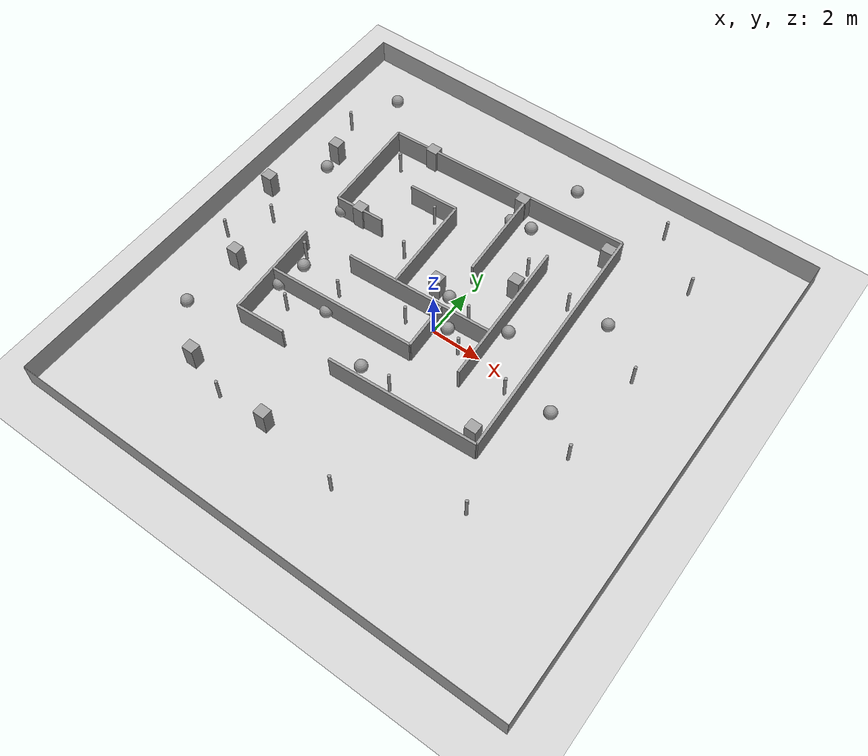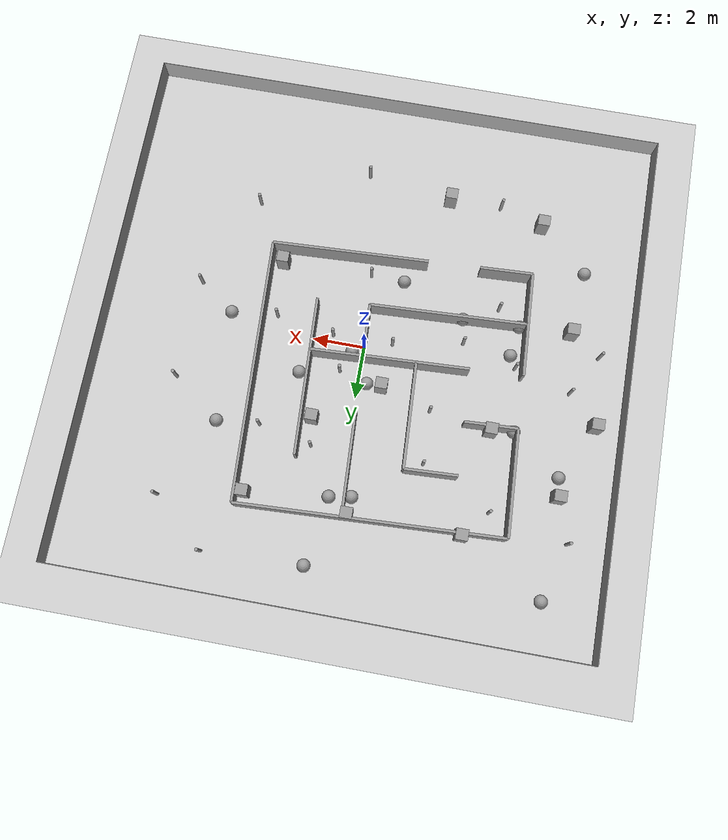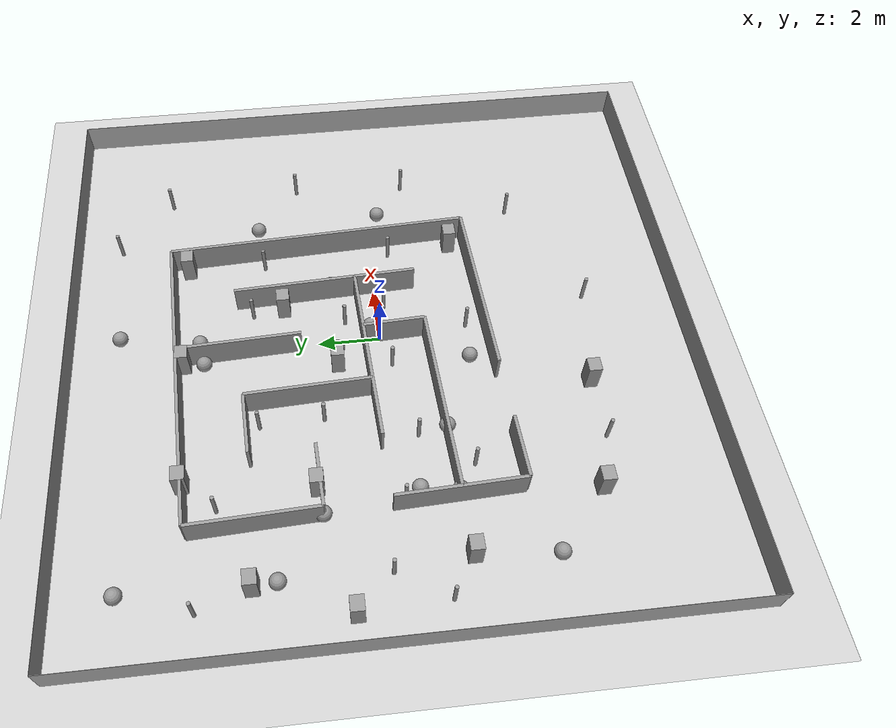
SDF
<sdf version="1.7">
 <world name="default">
  <physics type="ode">
   <max_step_size>0.004</max_step_size>
   <real_time_factor>1</real_time_factor>
   <real_time_update_rate>250</real_time_update_rate>
  </physics>
  <plugin name="gz::sim::systems::Physics" filename="gz-sim-physics-system"/>
  <plugin name="gz::sim::systems::UserCommands" filename="gz-sim-user-commands-system"/>
  <plugin name="gz::sim::systems::SceneBroadcaster" filename="gz-sim-scene-broadcaster-system"/>
  <plugin name="gz::sim::systems::Contact" filename="gz-sim-contact-system"/>
  <plugin name="gz::sim::systems::Imu" filename="gz-sim-imu-system"/>
  <plugin name="gz::sim::systems::Magnetometer" filename="gz-sim-magnetometer-system"/>
  <plugin name="gz::sim::systems::Altimeter" filename="gz-sim-altimeter-system"/>
  <plugin name="gz::sim::systems::NavSat" filename="gz-sim-navsat-system"/>
  <plugin name="gz::sim::systems::Sensors" filename="gz-sim-sensors-system">
   <render_engine>ogre2</render_engine>
  </plugin>
  <gravity>0 0 -9.8</gravity>
  <magnetic_field>6e-06 2.3e-05 -4.2e-05</magnetic_field>
  <atmosphere type="adiabatic"/>
  <spherical_coordinates>
   <surface_model>EARTH_WGS84</surface_model>
   <latitude_deg>39.7948</latitude_deg>
   <longitude_deg>-84.0863</longitude_deg>
   <elevation>265.2</elevation>
   <heading_deg>0</heading_deg>
  </spherical_coordinates>
  <scene>
   <grid>1</grid>
   <ambient>0.4 0.4 0.4 1</ambient>
   <background>0.7 0.7 0.7 1</background>
   <shadows>0</shadows>
  </scene>
  <light name="sunUTC" type="directional">
   <pose>0 0 500 0 -0 0</pose>
   <cast_shadows>0</cast_shadows>
   <direction>0.001 0.625 -0.78</direction>
   <diffuse>0.904 0.904 0.904 1</diffuse>
   <specular>0.271 0.271 0.271 1</specular>
   <attenuation><range>2000</range><linear>0</linear><constant>1</constant><quadratic>0</quadratic></attenuation>
   <spot><inner_angle>0</inner_angle><outer_angle>0</outer_angle><falloff>0</falloff></spot>
   <intensity>1</intensity>
  </light>
  <model name="ground_plane">
   <static>1</static>
   <link name="link">
    <collision name="collision">
     <geometry><plane><normal>0 0 1</normal><size>1 1</size></plane></geometry>
    </collision>
    <visual name="visual">
     <geometry><plane><normal>0 0 1</normal><size>100 100</size></plane></geometry>
     <material>
      <ambient>0.8 0.8 0.8 1</ambient>
      <diffuse>0.8 0.8 0.8 1</diffuse>
      <specular>0.8 0.8 0.8 1</specular>
     </material>
    </visual>
    <inertial>
     <mass>1</mass>
     <inertia><ixx>1</ixx><ixy>0</ixy><ixz>0</ixz><iyy>1</iyy><iyz>0</iyz><izz>1</izz></inertia>
    </inertial>
   </link>
  </model>
  <model name="wall_1">
   <pose>-10 0 0.5 0 0 -1.57</pose>
   <static>1</static>
   <link name="link">
    <collision name="collision"><geometry><box><size>20 0.01 1</size></box></geometry></collision>
    <visual name="visual">
     <geometry><box><size>20 0.01 1</size></box></geometry>
     <material>
      <ambient>0.7 0.7 0.7 1</ambient>
      <diffuse>0.7 0.7 0.7 1</diffuse>
      <specular>0.7 0.7 0.7 1</specular>
     </material>
    </visual>
    <inertial>
     <mass>1</mass>
     <inertia><ixx>1</ixx><ixy>0</ixy><ixz>0</ixz><iyy>1</iyy><iyz>0</iyz><izz>1</izz></inertia>
    </inertial>
   </link>
  </model>
  <model name="wall_2">
   <pose>10 0 0.5 0 0 -1.57</pose>
   <static>1</static>
   <link name="link">
    <collision name="collision"><geometry><box><size>20 0.01 1</size></box></geometry></collision>
    <visual name="visual">
     <geometry><box><size>20 0.01 1</size></box></geometry>
     <material>
      <ambient>0.7 0.7 0.7 1</ambient>
      <diffuse>0.7 0.7 0.7 1</diffuse>
      <specular>0.7 0.7 0.7 1</specular>
     </material>
    </visual>
    <inertial>
     <mass>1</mass>
     <inertia><ixx>1</ixx><ixy>0</ixy><ixz>0</ixz><iyy>1</iyy><iyz>0</iyz><izz>1</izz></inertia>
    </inertial>
   </link>
  </model>
  <model name="wall_3">
   <pose>0 10 0.5 0 -0 0</pose>
   <static>1</static>
   <link name="link">
    <collision name="collision"><geometry><box><size>20 0.01 1</size></box></geometry></collision>
    <visual name="visual">
     <geometry><box><size>20 0.01 1</size></box></geometry>
     <material>
      <ambient>0.7 0.7 0.7 1</ambient>
      <diffuse>0.7 0.7 0.7 1</diffuse>
      <specular>0.7 0.7 0.7 1</specular>
     </material>
    </visual>
    <inertial>
     <mass>1</mass>
     <inertia><ixx>1</ixx><ixy>0</ixy><ixz>0</ixz><iyy>1</iyy><iyz>0</iyz><izz>1</izz></inertia>
    </inertial>
   </link>
  </model>
  <model name="wall_4">
   <pose>0 -10 0.5 0 -0 0</pose>
   <static>1</static>
   <link name="link">
    <collision name="collision"><geometry><box><size>20 0.01 1</size></box></geometry></collision>
    <visual name="visual">
     <geometry><box><size>20 0.01 1</size></box></geometry>
     <material>
      <ambient>0.7 0.7 0.7 1</ambient>
      <diffuse>0.7 0.7 0.7 1</diffuse>
      <specular>0.7 0.7 0.7 1</specular>
     </material>
    </visual>
    <inertial>
     <mass>1</mass>
     <inertia><ixx>1</ixx><ixy>0</ixy><ixz>0</ixz><iyy>1</iyy><iyz>0</iyz><izz>1</izz></inertia>
    </inertial>
   </link>
  </model>
  <model name="s_maze">
   <link name="link_0_clone">
    <inertial>
     <mass>2000</mass>
     <inertia><ixx>16833.3</ixx><ixy>0</ixy><ixz>0</ixz><iyy>168.333</iyy><iyz>0</iyz><izz>16668.3</izz></inertia>
    </inertial>
    <pose>5 0 0 0 -0 0</pose>
    <visual name="visual">
     <geometry><box><size>0.1 10 1</size></box></geometry>
     <material>
      <lighting>1</lighting>
      <script><uri>file://media/materials/scripts/gazebo.material</uri><name>Gazebo/Grey</name></script>
      <shader type="vertex"><normal_map>__default__</normal_map></shader>
      <ambient>0.3 0.3 0.3 1</ambient>
      <diffuse>0.7 0.7 0.7 1</diffuse>
      <specular>0.01 0.01 0.01 1</specular>
      <emissive>0 0 0 1</emissive>
     </material>
    </visual>
    <collision name="collision">
     <geometry><box><size>0.1 10 1</size></box></geometry>
     <surface>
      <friction>
       <ode><mu>1</mu><mu2>1</mu2><fdir1>0 0 0</fdir1><slip1>0</slip1><slip2>0</slip2></ode>
       <torsional>
        <coefficient>1</coefficient>
        <patch_radius>0</patch_radius>
        <surface_radius>0</surface_radius>
        <use_patch_radius>1</use_patch_radius>
        <ode><slip>0</slip></ode>
       </torsional>
      </friction>
      <bounce><restitution_coefficient>0</restitution_coefficient><threshold>1e+06</threshold></bounce>
      <contact>
       <collide_without_contact>0</collide_without_contact>
       <collide_without_contact_bitmask>1</collide_without_contact_bitmask>
       <collide_bitmask>1</collide_bitmask>
       <ode>
        <soft_cfm>0</soft_cfm>
        <soft_erp>0.2</soft_erp>
        <kp>1e+13</kp>
        <kd>1</kd>
        <max_vel>0.01</max_vel>
        <min_depth>0</min_depth>
       </ode>
       <bullet>
        <split_impulse>1</split_impulse>
        <split_impulse_penetration_threshold>-0.01</split_impulse_penetration_threshold>
        <soft_cfm>0</soft_cfm>
        <soft_erp>0.2</soft_erp>
        <kp>1e+13</kp>
        <kd>1</kd>
       </bullet>
      </contact>
     </surface>
    </collision>
   </link>
   <link name="link_0_clone_0_clone">
    <inertial>
     <mass>400</mass>
     <inertia><ixx>166.667</ixx><ixy>0</ixy><ixz>0</ixz><iyy>33.6667</iyy><iyz>0</iyz><izz>133.667</izz></inertia>
    </inertial>
    <pose>1 -2 -0 0 -0 0</pose>
    <visual name="visual">
     <geometry><box><size>0.1 2 1</size></box></geometry>
     <material>
      <lighting>1</lighting>
      <script><uri>file://media/materials/scripts/gazebo.material</uri><name>Gazebo/Grey</name></script>
      <shader type="vertex"><normal_map>__default__</normal_map></shader>
      <ambient>0.3 0.3 0.3 1</ambient>
      <diffuse>0.7 0.7 0.7 1</diffuse>
      <specular>0.01 0.01 0.01 1</specular>
      <emissive>0 0 0 1</emissive>
     </material>
    </visual>
    <collision name="collision">
     <geometry><box><size>0.1 2 1</size></box></geometry>
     <surface>
      <friction>
       <ode><mu>1</mu><mu2>1</mu2><fdir1>0 0 0</fdir1><slip1>0</slip1><slip2>0</slip2></ode>
       <torsional>
        <coefficient>1</coefficient>
        <patch_radius>0</patch_radius>
        <surface_radius>0</surface_radius>
        <use_patch_radius>1</use_patch_radius>
        <ode><slip>0</slip></ode>
       </torsional>
      </friction>
      <bounce><restitution_coefficient>0</restitution_coefficient><threshold>1e+06</threshold></bounce>
      <contact>
       <collide_without_contact>0</collide_without_contact>
       <collide_without_contact_bitmask>1</collide_without_contact_bitmask>
       <collide_bitmask>1</collide_bitmask>
       <ode>
        <soft_cfm>0</soft_cfm>
        <soft_erp>0.2</soft_erp>
        <kp>1e+13</kp>
        <kd>1</kd>
        <max_vel>0.01</max_vel>
        <min_depth>0</min_depth>
       </ode>
       <bullet>
        <split_impulse>1</split_impulse>
        <split_impulse_penetration_threshold>-0.01</split_impulse_penetration_threshold>
        <soft_cfm>0</soft_cfm>
        <soft_erp>0.2</soft_erp>
        <kp>1e+13</kp>
        <kd>1</kd>
       </bullet>
      </contact>
     </surface>
    </collision>
   </link>
   <link name="link_0_clone_1_clone">
    <inertial>
     <mass>2000</mass>
     <inertia><ixx>16833.3</ixx><ixy>0</ixy><ixz>0</ixz><iyy>168.333</iyy><iyz>0</iyz><izz>16668.3</izz></inertia>
    </inertial>
    <pose>-0 5 -0 0 -0 1.5708</pose>
    <visual name="visual">
     <geometry><box><size>0.1 10 1</size></box></geometry>
     <material>
      <lighting>1</lighting>
      <script><uri>file://media/materials/scripts/gazebo.material</uri><name>Gazebo/Grey</name></script>
      <shader type="vertex"><normal_map>__default__</normal_map></shader>
      <ambient>0.3 0.3 0.3 1</ambient>
      <diffuse>0.7 0.7 0.7 1</diffuse>
      <specular>0.01 0.01 0.01 1</specular>
      <emissive>0 0 0 1</emissive>
     </material>
    </visual>
    <collision name="collision">
     <geometry><box><size>0.1 10 1</size></box></geometry>
     <surface>
      <friction>
       <ode><mu>1</mu><mu2>1</mu2><fdir1>0 0 0</fdir1><slip1>0</slip1><slip2>0</slip2></ode>
       <torsional>
        <coefficient>1</coefficient>
        <patch_radius>0</patch_radius>
        <surface_radius>0</surface_radius>
        <use_patch_radius>1</use_patch_radius>
        <ode><slip>0</slip></ode>
       </torsional>
      </friction>
      <bounce><restitution_coefficient>0</restitution_coefficient><threshold>1e+06</threshold></bounce>
      <contact>
       <collide_without_contact>0</collide_without_contact>
       <collide_without_contact_bitmask>1</collide_without_contact_bitmask>
       <collide_bitmask>1</collide_bitmask>
       <ode>
        <soft_cfm>0</soft_cfm>
        <soft_erp>0.2</soft_erp>
        <kp>1e+13</kp>
        <kd>1</kd>
        <max_vel>0.01</max_vel>
        <min_depth>0</min_depth>
       </ode>
       <bullet>
        <split_impulse>1</split_impulse>
        <split_impulse_penetration_threshold>-0.01</split_impulse_penetration_threshold>
        <soft_cfm>0</soft_cfm>
        <soft_erp>0.2</soft_erp>
        <kp>1e+13</kp>
        <kd>1</kd>
       </bullet>
      </contact>
     </surface>
    </collision>
   </link>
   <link name="link_0_clone_1_clone_0">
    <inertial>
     <mass>1200</mass>
     <inertia><ixx>3700</ixx><ixy>0</ixy><ixz>0</ixz><iyy>101</iyy><iyz>0</iyz><izz>3601</izz></inertia>
    </inertial>
    <pose>-2 -3 -0 0 -0 1.5708</pose>
    <visual name="visual">
     <geometry><box><size>0.1 6 1</size></box></geometry>
     <material>
      <lighting>1</lighting>
      <script><uri>file://media/materials/scripts/gazebo.material</uri><name>Gazebo/Grey</name></script>
      <shader type="vertex"><normal_map>__default__</normal_map></shader>
      <ambient>0.3 0.3 0.3 1</ambient>
      <diffuse>0.7 0.7 0.7 1</diffuse>
      <specular>0.01 0.01 0.01 1</specular>
      <emissive>0 0 0 1</emissive>
     </material>
    </visual>
    <collision name="collision">
     <geometry><box><size>0.1 6 1</size></box></geometry>
     <surface>
      <friction>
       <ode><mu>1</mu><mu2>1</mu2><fdir1>0 0 0</fdir1><slip1>0</slip1><slip2>0</slip2></ode>
       <torsional>
        <coefficient>1</coefficient>
        <patch_radius>0</patch_radius>
        <surface_radius>0</surface_radius>
        <use_patch_radius>1</use_patch_radius>
        <ode><slip>0</slip></ode>
       </torsional>
      </friction>
      <bounce><restitution_coefficient>0</restitution_coefficient><threshold>1e+06</threshold></bounce>
      <contact>
       <collide_without_contact>0</collide_without_contact>
       <collide_without_contact_bitmask>1</collide_without_contact_bitmask>
       <collide_bitmask>1</collide_bitmask>
       <ode>
        <soft_cfm>0</soft_cfm>
        <soft_erp>0.2</soft_erp>
        <kp>1e+13</kp>
        <kd>1</kd>
        <max_vel>0.01</max_vel>
        <min_depth>0</min_depth>
       </ode>
       <bullet>
        <split_impulse>1</split_impulse>
        <split_impulse_penetration_threshold>-0.01</split_impulse_penetration_threshold>
        <soft_cfm>0</soft_cfm>
        <soft_erp>0.2</soft_erp>
        <kp>1e+13</kp>
        <kd>1</kd>
       </bullet>
      </contact>
     </surface>
    </collision>
   </link>
   <link name="link_0_clone_1_clone_0_clone">
    <inertial>
     <mass>1200</mass>
     <inertia><ixx>3700</ixx><ixy>0</ixy><ixz>0</ixz><iyy>101</iyy><iyz>0</iyz><izz>3601</izz></inertia>
    </inertial>
    <pose>-0 -1 0 0 -0 1.5708</pose>
    <visual name="visual">
     <geometry><box><size>0.1 6 1</size></box></geometry>
     <material>
      <lighting>1</lighting>
      <script><uri>file://media/materials/scripts/gazebo.material</uri><name>Gazebo/Grey</name></script>
      <shader type="vertex"><normal_map>__default__</normal_map></shader>
      <ambient>0.3 0.3 0.3 1</ambient>
      <diffuse>0.7 0.7 0.7 1</diffuse>
      <specular>0.01 0.01 0.01 1</specular>
      <emissive>0 0 0 1</emissive>
     </material>
    </visual>
    <collision name="collision">
     <geometry><box><size>0.1 6 1</size></box></geometry>
     <surface>
      <friction>
       <ode><mu>1</mu><mu2>1</mu2><fdir1>0 0 0</fdir1><slip1>0</slip1><slip2>0</slip2></ode>
       <torsional>
        <coefficient>1</coefficient>
        <patch_radius>0</patch_radius>
        <surface_radius>0</surface_radius>
        <use_patch_radius>1</use_patch_radius>
        <ode><slip>0</slip></ode>
       </torsional>
      </friction>
      <bounce><restitution_coefficient>0</restitution_coefficient><threshold>1e+06</threshold></bounce>
      <contact>
       <collide_without_contact>0</collide_without_contact>
       <collide_without_contact_bitmask>1</collide_without_contact_bitmask>
       <collide_bitmask>1</collide_bitmask>
       <ode>
        <soft_cfm>0</soft_cfm>
        <soft_erp>0.2</soft_erp>
        <kp>1e+13</kp>
        <kd>1</kd>
        <max_vel>0.01</max_vel>
        <min_depth>0</min_depth>
       </ode>
       <bullet>
        <split_impulse>1</split_impulse>
        <split_impulse_penetration_threshold>-0.01</split_impulse_penetration_threshold>
        <soft_cfm>0</soft_cfm>
        <soft_erp>0.2</soft_erp>
        <kp>1e+13</kp>
        <kd>1</kd>
       </bullet>
      </contact>
     </surface>
    </collision>
   </link>
   <link name="link_0_clone_1_clone_0_clone_0">
    <inertial>
     <mass>1200</mass>
     <inertia><ixx>3700</ixx><ixy>0</ixy><ixz>0</ixz><iyy>101</iyy><iyz>0</iyz><izz>3601</izz></inertia>
    </inertial>
    <pose>2 -5 0 -0.004588 -0.005224 1.5715</pose>
    <visual name="visual">
     <geometry><box><size>0.1 6 1</size></box></geometry>
     <material>
      <lighting>1</lighting>
      <script><uri>file://media/materials/scripts/gazebo.material</uri><name>Gazebo/Grey</name></script>
      <shader type="vertex"><normal_map>__default__</normal_map></shader>
      <ambient>0.3 0.3 0.3 1</ambient>
      <diffuse>0.7 0.7 0.7 1</diffuse>
      <specular>0.01 0.01 0.01 1</specular>
      <emissive>0 0 0 1</emissive>
     </material>
    </visual>
    <collision name="collision">
     <geometry><box><size>0.1 6 1</size></box></geometry>
     <surface>
      <friction>
       <ode><mu>1</mu><mu2>1</mu2><fdir1>0 0 0</fdir1><slip1>0</slip1><slip2>0</slip2></ode>
       <torsional>
        <coefficient>1</coefficient>
        <patch_radius>0</patch_radius>
        <surface_radius>0</surface_radius>
        <use_patch_radius>1</use_patch_radius>
        <ode><slip>0</slip></ode>
       </torsional>
      </friction>
      <bounce><restitution_coefficient>0</restitution_coefficient><threshold>1e+06</threshold></bounce>
      <contact>
       <collide_without_contact>0</collide_without_contact>
       <collide_without_contact_bitmask>1</collide_without_contact_bitmask>
       <collide_bitmask>1</collide_bitmask>
       <ode>
        <soft_cfm>0</soft_cfm>
        <soft_erp>0.2</soft_erp>
        <kp>1e+13</kp>
        <kd>1</kd>
        <max_vel>0.01</max_vel>
        <min_depth>0</min_depth>
       </ode>
       <bullet>
        <split_impulse>1</split_impulse>
        <split_impulse_penetration_threshold>-0.01</split_impulse_penetration_threshold>
        <soft_cfm>0</soft_cfm>
        <soft_erp>0.2</soft_erp>
        <kp>1e+13</kp>
        <kd>1</kd>
       </bullet>
      </contact>
     </surface>
    </collision>
   </link>
   <link name="link_0_clone_1_clone_0_clone_clone">
    <inertial>
     <mass>400</mass>
     <inertia><ixx>166.667</ixx><ixy>0</ixy><ixz>0</ixz><iyy>33.6667</iyy><iyz>0</iyz><izz>133.667</izz></inertia>
    </inertial>
    <pose>-2 3 -0 0 -0 1.5708</pose>
    <visual name="visual">
     <geometry><box><size>0.1 2 1</size></box></geometry>
     <material>
      <lighting>1</lighting>
      <script><uri>file://media/materials/scripts/gazebo.material</uri><name>Gazebo/Grey</name></script>
      <shader type="vertex"><normal_map>__default__</normal_map></shader>
      <ambient>0.3 0.3 0.3 1</ambient>
      <diffuse>0.7 0.7 0.7 1</diffuse>
      <specular>0.01 0.01 0.01 1</specular>
      <emissive>0 0 0 1</emissive>
     </material>
    </visual>
    <collision name="collision">
     <geometry><box><size>0.1 2 1</size></box></geometry>
     <surface>
      <friction>
       <ode><mu>1</mu><mu2>1</mu2><fdir1>0 0 0</fdir1><slip1>0</slip1><slip2>0</slip2></ode>
       <torsional>
        <coefficient>1</coefficient>
        <patch_radius>0</patch_radius>
        <surface_radius>0</surface_radius>
        <use_patch_radius>1</use_patch_radius>
        <ode><slip>0</slip></ode>
       </torsional>
      </friction>
      <bounce><restitution_coefficient>0</restitution_coefficient><threshold>1e+06</threshold></bounce>
      <contact>
       <collide_without_contact>0</collide_without_contact>
       <collide_without_contact_bitmask>1</collide_without_contact_bitmask>
       <collide_bitmask>1</collide_bitmask>
       <ode>
        <soft_cfm>0</soft_cfm>
        <soft_erp>0.2</soft_erp>
        <kp>1e+13</kp>
        <kd>1</kd>
        <max_vel>0.01</max_vel>
        <min_depth>0</min_depth>
       </ode>
       <bullet>
        <split_impulse>1</split_impulse>
        <split_impulse_penetration_threshold>-0.01</split_impulse_penetration_threshold>
        <soft_cfm>0</soft_cfm>
        <soft_erp>0.2</soft_erp>
        <kp>1e+13</kp>
        <kd>1</kd>
       </bullet>
      </contact>
     </surface>
    </collision>
   </link>
   <link name="link_0_clone_1_clone_0_clone_clone_clone">
    <inertial>
     <mass>400</mass>
     <inertia><ixx>166.667</ixx><ixy>0</ixy><ixz>0</ixz><iyy>33.6667</iyy><iyz>0</iyz><izz>133.667</izz></inertia>
    </inertial>
    <pose>-4 1 0 0 -0 1.5708</pose>
    <visual name="visual">
     <geometry><box><size>0.1 2 1</size></box></geometry>
     <material>
      <lighting>1</lighting>
      <script><uri>file://media/materials/scripts/gazebo.material</uri><name>Gazebo/Grey</name></script>
      <shader type="vertex"><normal_map>__default__</normal_map></shader>
      <ambient>0.3 0.3 0.3 1</ambient>
      <diffuse>0.7 0.7 0.7 1</diffuse>
      <specular>0.01 0.01 0.01 1</specular>
      <emissive>0 0 0 1</emissive>
     </material>
    </visual>
    <collision name="collision">
     <geometry><box><size>0.1 2 1</size></box></geometry>
     <surface>
      <friction>
       <ode><mu>1</mu><mu2>1</mu2><fdir1>0 0 0</fdir1><slip1>0</slip1><slip2>0</slip2></ode>
       <torsional>
        <coefficient>1</coefficient>
        <patch_radius>0</patch_radius>
        <surface_radius>0</surface_radius>
        <use_patch_radius>1</use_patch_radius>
        <ode><slip>0</slip></ode>
       </torsional>
      </friction>
      <bounce><restitution_coefficient>0</restitution_coefficient><threshold>1e+06</threshold></bounce>
      <contact>
       <collide_without_contact>0</collide_without_contact>
       <collide_without_contact_bitmask>1</collide_without_contact_bitmask>
       <collide_bitmask>1</collide_bitmask>
       <ode>
        <soft_cfm>0</soft_cfm>
        <soft_erp>0.2</soft_erp>
        <kp>1e+13</kp>
        <kd>1</kd>
        <max_vel>0.01</max_vel>
        <min_depth>0</min_depth>
       </ode>
       <bullet>
        <split_impulse>1</split_impulse>
        <split_impulse_penetration_threshold>-0.01</split_impulse_penetration_threshold>
        <soft_cfm>0</soft_cfm>
        <soft_erp>0.2</soft_erp>
        <kp>1e+13</kp>
        <kd>1</kd>
       </bullet>
      </contact>
     </surface>
    </collision>
   </link>
   <link name="link_0_clone_1_clone_0_clone_clone_clone_0">
    <inertial>
     <mass>400</mass>
     <inertia><ixx>166.667</ixx><ixy>0</ixy><ixz>0</ixz><iyy>33.6667</iyy><iyz>0</iyz><izz>133.667</izz></inertia>
    </inertial>
    <pose>-4 -5 -0 -0.004588 -0.005224 1.5715</pose>
    <visual name="visual">
     <geometry><box><size>0.1 2 1</size></box></geometry>
     <material>
      <lighting>1</lighting>
      <script><uri>file://media/materials/scripts/gazebo.material</uri><name>Gazebo/Grey</name></script>
      <shader type="vertex"><normal_map>__default__</normal_map></shader>
      <ambient>0.3 0.3 0.3 1</ambient>
      <diffuse>0.7 0.7 0.7 1</diffuse>
      <specular>0.01 0.01 0.01 1</specular>
      <emissive>0 0 0 1</emissive>
     </material>
    </visual>
    <collision name="collision">
     <geometry><box><size>0.1 2 1</size></box></geometry>
     <surface>
      <friction>
       <ode><mu>1</mu><mu2>1</mu2><fdir1>0 0 0</fdir1><slip1>0</slip1><slip2>0</slip2></ode>
       <torsional>
        <coefficient>1</coefficient>
        <patch_radius>0</patch_radius>
        <surface_radius>0</surface_radius>
        <use_patch_radius>1</use_patch_radius>
        <ode><slip>0</slip></ode>
       </torsional>
      </friction>
      <bounce><restitution_coefficient>0</restitution_coefficient><threshold>1e+06</threshold></bounce>
      <contact>
       <collide_without_contact>0</collide_without_contact>
       <collide_without_contact_bitmask>1</collide_without_contact_bitmask>
       <collide_bitmask>1</collide_bitmask>
       <ode>
        <soft_cfm>0</soft_cfm>
        <soft_erp>0.2</soft_erp>
        <kp>1e+13</kp>
        <kd>1</kd>
        <max_vel>0.01</max_vel>
        <min_depth>0</min_depth>
       </ode>
       <bullet>
        <split_impulse>1</split_impulse>
        <split_impulse_penetration_threshold>-0.01</split_impulse_penetration_threshold>
        <soft_cfm>0</soft_cfm>
        <soft_erp>0.2</soft_erp>
        <kp>1e+13</kp>
        <kd>1</kd>
       </bullet>
      </contact>
     </surface>
    </collision>
   </link>
   <link name="link_0_clone_2">
    <inertial>
     <mass>1200</mass>
     <inertia><ixx>3700</ixx><ixy>0</ixy><ixz>0</ixz><iyy>101</iyy><iyz>0</iyz><izz>3601</izz></inertia>
    </inertial>
    <pose>3 -0 -0 0 -0 0</pose>
    <visual name="visual">
     <geometry><box><size>0.1 6 1</size></box></geometry>
     <material>
      <lighting>1</lighting>
      <script><uri>file://media/materials/scripts/gazebo.material</uri><name>Gazebo/Grey</name></script>
      <shader type="vertex"><normal_map>__default__</normal_map></shader>
      <ambient>0.3 0.3 0.3 1</ambient>
      <diffuse>0.7 0.7 0.7 1</diffuse>
      <specular>0.01 0.01 0.01 1</specular>
      <emissive>0 0 0 1</emissive>
     </material>
    </visual>
    <collision name="collision">
     <geometry><box><size>0.1 6 1</size></box></geometry>
     <surface>
      <friction>
       <ode><mu>1</mu><mu2>1</mu2><fdir1>0 0 0</fdir1><slip1>0</slip1><slip2>0</slip2></ode>
       <torsional>
        <coefficient>1</coefficient>
        <patch_radius>0</patch_radius>
        <surface_radius>0</surface_radius>
        <use_patch_radius>1</use_patch_radius>
        <ode><slip>0</slip></ode>
       </torsional>
      </friction>
      <bounce><restitution_coefficient>0</restitution_coefficient><threshold>1e+06</threshold></bounce>
      <contact>
       <collide_without_contact>0</collide_without_contact>
       <collide_without_contact_bitmask>1</collide_without_contact_bitmask>
       <collide_bitmask>1</collide_bitmask>
       <ode>
        <soft_cfm>0</soft_cfm>
        <soft_erp>0.2</soft_erp>
        <kp>1e+13</kp>
        <kd>1</kd>
        <max_vel>0.01</max_vel>
        <min_depth>0</min_depth>
       </ode>
       <bullet>
        <split_impulse>1</split_impulse>
        <split_impulse_penetration_threshold>-0.01</split_impulse_penetration_threshold>
        <soft_cfm>0</soft_cfm>
        <soft_erp>0.2</soft_erp>
        <kp>1e+13</kp>
        <kd>1</kd>
       </bullet>
      </contact>
     </surface>
    </collision>
   </link>
   <link name="link_0_clone_2_clone">
    <inertial>
     <mass>0.188114</mass>
     <inertia>
      <ixx>0.0313523</ixx>
      <ixy>0</ixy>
      <ixz>0</ixz>
      <iyy>0.0162309</iyy>
      <iyz>0</iyz>
      <izz>0.0162309</izz>
     </inertia>
    </inertial>
    <pose>-1 1 0 0 -0 0</pose>
    <visual name="visual">
     <geometry><box><size>0.1 4 1</size></box></geometry>
     <material>
      <lighting>1</lighting>
      <script><uri>file://media/materials/scripts/gazebo.material</uri><name>Gazebo/Grey</name></script>
      <shader type="vertex"><normal_map>__default__</normal_map></shader>
      <ambient>0.3 0.3 0.3 1</ambient>
      <diffuse>0.7 0.7 0.7 1</diffuse>
      <specular>0.01 0.01 0.01 1</specular>
      <emissive>0 0 0 1</emissive>
     </material>
    </visual>
    <collision name="collision">
     <geometry><box><size>0.1 4 1</size></box></geometry>
     <surface>
      <friction>
       <ode><mu>1</mu><mu2>1</mu2><fdir1>0 0 0</fdir1><slip1>0</slip1><slip2>0</slip2></ode>
       <torsional>
        <coefficient>1</coefficient>
        <patch_radius>0</patch_radius>
        <surface_radius>0</surface_radius>
        <use_patch_radius>1</use_patch_radius>
        <ode><slip>0</slip></ode>
       </torsional>
      </friction>
      <bounce><restitution_coefficient>0</restitution_coefficient><threshold>1e+06</threshold></bounce>
      <contact>
       <collide_without_contact>0</collide_without_contact>
       <collide_without_contact_bitmask>1</collide_without_contact_bitmask>
       <collide_bitmask>1</collide_bitmask>
       <ode>
        <soft_cfm>0</soft_cfm>
        <soft_erp>0.2</soft_erp>
        <kp>1e+13</kp>
        <kd>1</kd>
        <max_vel>0.01</max_vel>
        <min_depth>0</min_depth>
       </ode>
       <bullet>
        <split_impulse>1</split_impulse>
        <split_impulse_penetration_threshold>-0.01</split_impulse_penetration_threshold>
        <soft_cfm>0</soft_cfm>
        <soft_erp>0.2</soft_erp>
        <kp>1e+13</kp>
        <kd>1</kd>
       </bullet>
      </contact>
     </surface>
    </collision>
   </link>
   <link name="link_0_clone_2_clone_clone">
    <inertial>
     <mass>800</mass>
     <inertia><ixx>1133.33</ixx><ixy>0</ixy><ixz>0</ixz><iyy>67.3333</iyy><iyz>0</iyz><izz>1067.33</izz></inertia>
    </inertial>
    <pose>1 3 -0 0 -0 0</pose>
    <visual name="visual">
     <geometry><box><size>0.1 4 1</size></box></geometry>
     <material>
      <lighting>1</lighting>
      <script><uri>file://media/materials/scripts/gazebo.material</uri><name>Gazebo/Grey</name></script>
      <shader type="vertex"><normal_map>__default__</normal_map></shader>
      <ambient>0.3 0.3 0.3 1</ambient>
      <diffuse>0.7 0.7 0.7 1</diffuse>
      <specular>0.01 0.01 0.01 1</specular>
      <emissive>0 0 0 1</emissive>
     </material>
    </visual>
    <collision name="collision">
     <geometry><box><size>0.1 4 1</size></box></geometry>
     <surface>
      <friction>
       <ode><mu>1</mu><mu2>1</mu2><fdir1>0 0 0</fdir1><slip1>0</slip1><slip2>0</slip2></ode>
       <torsional>
        <coefficient>1</coefficient>
        <patch_radius>0</patch_radius>
        <surface_radius>0</surface_radius>
        <use_patch_radius>1</use_patch_radius>
        <ode><slip>0</slip></ode>
       </torsional>
      </friction>
      <bounce><restitution_coefficient>0</restitution_coefficient><threshold>1e+06</threshold></bounce>
      <contact>
       <collide_without_contact>0</collide_without_contact>
       <collide_without_contact_bitmask>1</collide_without_contact_bitmask>
       <collide_bitmask>1</collide_bitmask>
       <ode>
        <soft_cfm>0</soft_cfm>
        <soft_erp>0.2</soft_erp>
        <kp>1e+13</kp>
        <kd>1</kd>
        <max_vel>0.01</max_vel>
        <min_depth>0</min_depth>
       </ode>
       <bullet>
        <split_impulse>1</split_impulse>
        <split_impulse_penetration_threshold>-0.01</split_impulse_penetration_threshold>
        <soft_cfm>0</soft_cfm>
        <soft_erp>0.2</soft_erp>
        <kp>1e+13</kp>
        <kd>1</kd>
       </bullet>
      </contact>
     </surface>
    </collision>
   </link>
   <link name="link_0_clone_2_clone_clone_0">
    <inertial>
     <mass>800</mass>
     <inertia><ixx>1133.33</ixx><ixy>0</ixy><ixz>0</ixz><iyy>67.3333</iyy><iyz>0</iyz><izz>1067.33</izz></inertia>
    </inertial>
    <pose>-5 3 -0 0.005224 -0.004588 0.000681</pose>
    <visual name="visual">
     <geometry><box><size>0.1 4 1</size></box></geometry>
     <material>
      <lighting>1</lighting>
      <script><uri>file://media/materials/scripts/gazebo.material</uri><name>Gazebo/Grey</name></script>
      <shader type="vertex"><normal_map>__default__</normal_map></shader>
      <ambient>0.3 0.3 0.3 1</ambient>
      <diffuse>0.7 0.7 0.7 1</diffuse>
      <specular>0.01 0.01 0.01 1</specular>
      <emissive>0 0 0 1</emissive>
     </material>
    </visual>
    <collision name="collision">
     <geometry><box><size>0.1 4 1</size></box></geometry>
     <surface>
      <friction>
       <ode><mu>1</mu><mu2>1</mu2><fdir1>0 0 0</fdir1><slip1>0</slip1><slip2>0</slip2></ode>
       <torsional>
        <coefficient>1</coefficient>
        <patch_radius>0</patch_radius>
        <surface_radius>0</surface_radius>
        <use_patch_radius>1</use_patch_radius>
        <ode><slip>0</slip></ode>
       </torsional>
      </friction>
      <bounce><restitution_coefficient>0</restitution_coefficient><threshold>1e+06</threshold></bounce>
      <contact>
       <collide_without_contact>0</collide_without_contact>
       <collide_without_contact_bitmask>1</collide_without_contact_bitmask>
       <collide_bitmask>1</collide_bitmask>
       <ode>
        <soft_cfm>0</soft_cfm>
        <soft_erp>0.2</soft_erp>
        <kp>1e+13</kp>
        <kd>1</kd>
        <max_vel>0.01</max_vel>
        <min_depth>0</min_depth>
       </ode>
       <bullet>
        <split_impulse>1</split_impulse>
        <split_impulse_penetration_threshold>-0.01</split_impulse_penetration_threshold>
        <soft_cfm>0</soft_cfm>
        <soft_erp>0.2</soft_erp>
        <kp>1e+13</kp>
        <kd>1</kd>
       </bullet>
      </contact>
     </surface>
    </collision>
   </link>
   <link name="link_0_clone_2_clone_clone_0_clone">
    <inertial>
     <mass>800</mass>
     <inertia><ixx>1133.33</ixx><ixy>0</ixy><ixz>0</ixz><iyy>67.3333</iyy><iyz>0</iyz><izz>1067.33</izz></inertia>
    </inertial>
    <pose>-5 -3 -0 0.010445 -0.009179 0.001338</pose>
    <visual name="visual">
     <geometry><box><size>0.1 4 1</size></box></geometry>
     <material>
      <lighting>1</lighting>
      <script><uri>file://media/materials/scripts/gazebo.material</uri><name>Gazebo/Grey</name></script>
      <shader type="vertex"><normal_map>__default__</normal_map></shader>
      <ambient>0.3 0.3 0.3 1</ambient>
      <diffuse>0.7 0.7 0.7 1</diffuse>
      <specular>0.01 0.01 0.01 1</specular>
      <emissive>0 0 0 1</emissive>
     </material>
    </visual>
    <collision name="collision">
     <geometry><box><size>0.1 4 1</size></box></geometry>
     <surface>
      <friction>
       <ode><mu>1</mu><mu2>1</mu2><fdir1>0 0 0</fdir1><slip1>0</slip1><slip2>0</slip2></ode>
       <torsional>
        <coefficient>1</coefficient>
        <patch_radius>0</patch_radius>
        <surface_radius>0</surface_radius>
        <use_patch_radius>1</use_patch_radius>
        <ode><slip>0</slip></ode>
       </torsional>
      </friction>
      <bounce><restitution_coefficient>0</restitution_coefficient><threshold>1e+06</threshold></bounce>
      <contact>
       <collide_without_contact>0</collide_without_contact>
       <collide_without_contact_bitmask>1</collide_without_contact_bitmask>
       <collide_bitmask>1</collide_bitmask>
       <ode>
        <soft_cfm>0</soft_cfm>
        <soft_erp>0.2</soft_erp>
        <kp>1e+13</kp>
        <kd>1</kd>
        <max_vel>0.01</max_vel>
        <min_depth>0</min_depth>
       </ode>
       <bullet>
        <split_impulse>1</split_impulse>
        <split_impulse_penetration_threshold>-0.01</split_impulse_penetration_threshold>
        <soft_cfm>0</soft_cfm>
        <soft_erp>0.2</soft_erp>
        <kp>1e+13</kp>
        <kd>1</kd>
       </bullet>
      </contact>
     </surface>
    </collision>
   </link>
   <static>0</static>
   <pose>-1.10067 1.49042 0.499698 -7.6e-05 1.5e-05 0.04861</pose>
  </model>
  <audio><device>default</device></audio>
  <model name="unit_box">
   <pose>-0.910709 1.44411 0.499996 -4e-05 -5.2e-05 -6.2e-05</pose>
   <link name="link">
    <inertial>
     <mass>1</mass>
     <inertia>
      <ixx>0.166667</ixx>
      <ixy>0</ixy>
      <ixz>0</ixz>
      <iyy>0.166667</iyy>
      <iyz>0</iyz>
      <izz>0.166667</izz>
     </inertia>
    </inertial>
    <collision name="collision"><geometry><box><size>0.459236 0.414137 1</size></box></geometry></collision>
    <visual name="visual">
     <geometry><box><size>0.459236 0.414137 1</size></box></geometry>
     <material>
      <script><name>Gazebo/Grey</name><uri>file://media/materials/scripts/gazebo.material</uri></script>
     </material>
    </visual>
   </link>
  </model>
  <model name="unit_box_clone">
   <pose>-0.483409 6.34886 0.499971 0.000103 3.2e-05 0.00013</pose>
   <link name="link">
    <inertial>
     <mass>1</mass>
     <inertia>
      <ixx>0.166667</ixx>
      <ixy>0</ixy>
      <ixz>0</ixz>
      <iyy>0.166667</iyy>
      <iyz>0</iyz>
      <izz>0.166667</izz>
     </inertia>
    </inertial>
    <collision name="collision"><geometry><box><size>0.459236 0.414137 1</size></box></geometry></collision>
    <visual name="visual">
     <geometry><box><size>0.459236 0.414137 1</size></box></geometry>
     <material>
      <script><name>Gazebo/Grey</name><uri>file://media/materials/scripts/gazebo.material</uri></script>
     </material>
    </visual>
   </link>
  </model>
  <model name="unit_box_clone_0">
   <pose>-5.18539 2.39276 0.499996 -4e-05 -5.2e-05 -3.4e-05</pose>
   <link name="link">
    <inertial>
     <mass>1</mass>
     <inertia>
      <ixx>0.166667</ixx>
      <ixy>0</ixy>
      <ixz>0</ixz>
      <iyy>0.166667</iyy>
      <iyz>0</iyz>
      <izz>0.166667</izz>
     </inertia>
    </inertial>
    <collision name="collision"><geometry><box><size>0.459236 0.414137 1</size></box></geometry></collision>
    <visual name="visual">
     <geometry><box><size>0.459236 0.414137 1</size></box></geometry>
     <material>
      <script><name>Gazebo/Grey</name><uri>file://media/materials/scripts/gazebo.material</uri></script>
     </material>
    </visual>
   </link>
  </model>
  <model name="unit_box_clone_1">
   <pose>-4.69438 6.38062 0.499996 -4e-05 5.2e-05 0.000173</pose>
   <link name="link">
    <inertial>
     <mass>1</mass>
     <inertia>
      <ixx>0.166667</ixx>
      <ixy>0</ixy>
      <ixz>0</ixz>
      <iyy>0.166667</iyy>
      <iyz>0</iyz>
      <izz>0.166667</izz>
     </inertia>
    </inertial>
    <collision name="collision"><geometry><box><size>0.459236 0.414137 1</size></box></geometry></collision>
    <visual name="visual">
     <geometry><box><size>0.459236 0.414137 1</size></box></geometry>
     <material>
      <script><name>Gazebo/Grey</name><uri>file://media/materials/scripts/gazebo.material</uri></script>
     </material>
    </visual>
   </link>
  </model>
  <model name="unit_box_clone_2">
   <pose>1.42791 3.06268 0.499971 0.000103 3.2e-05 0.000135</pose>
   <link name="link">
    <inertial>
     <mass>1</mass>
     <inertia>
      <ixx>0.166667</ixx>
      <ixy>0</ixy>
      <ixz>0</ixz>
      <iyy>0.166667</iyy>
      <iyz>0</iyz>
      <izz>0.166667</izz>
     </inertia>
    </inertial>
    <collision name="collision"><geometry><box><size>0.459236 0.414137 1</size></box></geometry></collision>
    <visual name="visual">
     <geometry><box><size>0.459236 0.414137 1</size></box></geometry>
     <material>
      <script><name>Gazebo/Grey</name><uri>file://media/materials/scripts/gazebo.material</uri></script>
     </material>
    </visual>
   </link>
  </model>
  <model name="unit_box_clone_3">
   <pose>3.39104 6.20706 0.5 0 -0 0.02507</pose>
   <link name="link">
    <inertial>
     <mass>1</mass>
     <inertia>
      <ixx>0.166667</ixx>
      <ixy>0</ixy>
      <ixz>0</ixz>
      <iyy>0.166667</iyy>
      <iyz>0</iyz>
      <izz>0.166667</izz>
     </inertia>
    </inertial>
    <collision name="collision"><geometry><box><size>0.459236 0.414137 1</size></box></geometry></collision>
    <visual name="visual">
     <geometry><box><size>0.459236 0.414137 1</size></box></geometry>
     <material>
      <script><name>Gazebo/Grey</name><uri>file://media/materials/scripts/gazebo.material</uri></script>
     </material>
    </visual>
   </link>
  </model>
  <model name="unit_box_clone_4">
   <pose>3.66268 -2.77384 0.499996 -4e-05 5.2e-05 0.000179</pose>
   <link name="link">
    <inertial>
     <mass>1</mass>
     <inertia>
      <ixx>0.166667</ixx>
      <ixy>0</ixy>
      <ixz>0</ixz>
      <iyy>0.166667</iyy>
      <iyz>0</iyz>
      <izz>0.166667</izz>
     </inertia>
    </inertial>
    <collision name="collision"><geometry><box><size>0.459236 0.414137 1</size></box></geometry></collision>
    <visual name="visual">
     <geometry><box><size>0.459236 0.414137 1</size></box></geometry>
     <material>
      <script><name>Gazebo/Grey</name><uri>file://media/materials/scripts/gazebo.material</uri></script>
     </material>
    </visual>
   </link>
  </model>
  <model name="unit_box_clone_5">
   <pose>-2.31514 -6.47687 0.499971 0.000103 3.2e-05 0.00014</pose>
   <link name="link">
    <inertial>
     <mass>1</mass>
     <inertia>
      <ixx>0.166667</ixx>
      <ixy>0</ixy>
      <ixz>0</ixz>
      <iyy>0.166667</iyy>
      <iyz>0</iyz>
      <izz>0.166667</izz>
     </inertia>
    </inertial>
    <collision name="collision"><geometry><box><size>0.459236 0.414137 1</size></box></geometry></collision>
    <visual name="visual">
     <geometry><box><size>0.459236 0.414137 1</size></box></geometry>
     <material>
      <script><name>Gazebo/Grey</name><uri>file://media/materials/scripts/gazebo.material</uri></script>
     </material>
    </visual>
   </link>
  </model>
  <model name="unit_box_clone_6">
   <pose>-6.00001 -5.99993 0.499996 -4e-05 -5.2e-05 -2.5e-05</pose>
   <link name="link">
    <inertial>
     <mass>1</mass>
     <inertia>
      <ixx>0.166667</ixx>
      <ixy>0</ixy>
      <ixz>0</ixz>
      <iyy>0.166667</iyy>
      <iyz>0</iyz>
      <izz>0.166667</izz>
     </inertia>
    </inertial>
    <collision name="collision"><geometry><box><size>0.459236 0.414137 1</size></box></geometry></collision>
    <visual name="visual">
     <geometry><box><size>0.459236 0.414137 1</size></box></geometry>
     <material>
      <script><name>Gazebo/Grey</name><uri>file://media/materials/scripts/gazebo.material</uri></script>
     </material>
    </visual>
   </link>
  </model>
  <model name="unit_box_clone_7">
   <pose>-7.67556 -1.87902 0.499996 -4e-05 -5.2e-05 -3.3e-05</pose>
   <link name="link">
    <inertial>
     <mass>1</mass>
     <inertia>
      <ixx>0.166667</ixx>
      <ixy>0</ixy>
      <ixz>0</ixz>
      <iyy>0.166667</iyy>
      <iyz>0</iyz>
      <izz>0.166667</izz>
     </inertia>
    </inertial>
    <collision name="collision"><geometry><box><size>0.459236 0.414137 1</size></box></geometry></collision>
    <visual name="visual">
     <geometry><box><size>0.459236 0.414137 1</size></box></geometry>
     <material>
      <script><name>Gazebo/Grey</name><uri>file://media/materials/scripts/gazebo.material</uri></script>
     </material>
    </visual>
   </link>
  </model>
  <model name="unit_box_clone_8">
   <pose>-7.99322 4.39185 0.499996 -4e-05 5.2e-05 0.000155</pose>
   <link name="link">
    <inertial>
     <mass>1</mass>
     <inertia>
      <ixx>0.166667</ixx>
      <ixy>0</ixy>
      <ixz>0</ixz>
      <iyy>0.166667</iyy>
      <iyz>0</iyz>
      <izz>0.166667</izz>
     </inertia>
    </inertial>
    <collision name="collision"><geometry><box><size>0.459236 0.414137 1</size></box></geometry></collision>
    <visual name="visual">
     <geometry><box><size>0.459236 0.414137 1</size></box></geometry>
     <material>
      <script><name>Gazebo/Grey</name><uri>file://media/materials/scripts/gazebo.material</uri></script>
     </material>
    </visual>
   </link>
  </model>
  <model name="unit_sphere">
   <pose>-5.53333 -0.615366 0.25201 0 -0 0</pose>
   <link name="link">
    <inertial>
     <mass>1</mass>
     <inertia><ixx>0.1</ixx><ixy>0</ixy><ixz>0</ixz><iyy>0.1</iyy><iyz>0</iyz><izz>0.1</izz></inertia>
    </inertial>
    <collision name="collision"><geometry><sphere><radius>0.25201</radius></sphere></geometry></collision>
    <visual name="visual">
     <geometry><sphere><radius>0.25201</radius></sphere></geometry>
     <material>
      <script><name>Gazebo/Grey</name><uri>file://media/materials/scripts/gazebo.material</uri></script>
     </material>
    </visual>
   </link>
  </model>
  <model name="unit_box_clone_9">
   <pose>-9.01649 1.55816 0.499996 -4e-05 -5.2e-05 -6.2e-05</pose>
   <link name="link">
    <inertial>
     <mass>1</mass>
     <inertia>
      <ixx>0.166667</ixx>
      <ixy>0</ixy>
      <ixz>0</ixz>
      <iyy>0.166667</iyy>
      <iyz>0</iyz>
      <izz>0.166667</izz>
     </inertia>
    </inertial>
    <collision name="collision"><geometry><box><size>0.459236 0.414137 1</size></box></geometry></collision>
    <visual name="visual">
     <geometry><box><size>0.459236 0.414137 1</size></box></geometry>
     <material>
      <script><name>Gazebo/Grey</name><uri>file://media/materials/scripts/gazebo.material</uri></script>
     </material>
    </visual>
   </link>
  </model>
  <model name="unit_sphere_clone">
   <pose>2.24987 1.4219 0.25201 0 -0 0</pose>
   <link name="link">
    <inertial>
     <mass>1</mass>
     <inertia><ixx>0.1</ixx><ixy>0</ixy><ixz>0</ixz><iyy>0.1</iyy><iyz>0</iyz><izz>0.1</izz></inertia>
    </inertial>
    <collision name="collision"><geometry><sphere><radius>0.25201</radius></sphere></geometry></collision>
    <visual name="visual">
     <geometry><sphere><radius>0.25201</radius></sphere></geometry>
     <material>
      <script><name>Gazebo/Grey</name><uri>file://media/materials/scripts/gazebo.material</uri></script>
     </material>
    </visual>
   </link>
  </model>
  <model name="unit_sphere_clone_0">
   <pose>0.278128 5.84538 0.25201 0 -0 0</pose>
   <link name="link">
    <inertial>
     <mass>1</mass>
     <inertia><ixx>0.1</ixx><ixy>0</ixy><ixz>0</ixz><iyy>0.1</iyy><iyz>0</iyz><izz>0.1</izz></inertia>
    </inertial>
    <collision name="collision"><geometry><sphere><radius>0.25201</radius></sphere></geometry></collision>
    <visual name="visual">
     <geometry><sphere><radius>0.25201</radius></sphere></geometry>
     <material>
      <script><name>Gazebo/Grey</name><uri>file://media/materials/scripts/gazebo.material</uri></script>
     </material>
    </visual>
   </link>
  </model>
  <model name="unit_sphere_clone_1">
   <pose>-0.550211 5.70816 0.25201 0 -0 0</pose>
   <link name="link">
    <inertial>
     <mass>1</mass>
     <inertia><ixx>0.1</ixx><ixy>0</ixy><ixz>0</ixz><iyy>0.1</iyy><iyz>0</iyz><izz>0.1</izz></inertia>
    </inertial>
    <collision name="collision"><geometry><sphere><radius>0.25201</radius></sphere></geometry></collision>
    <visual name="visual">
     <geometry><sphere><radius>0.25201</radius></sphere></geometry>
     <material>
      <script><name>Gazebo/Grey</name><uri>file://media/materials/scripts/gazebo.material</uri></script>
     </material>
    </visual>
   </link>
  </model>
  <model name="unit_sphere_clone_2">
   <pose>-1.08186 -2.8039 0.25201 0 -0 0</pose>
   <link name="link">
    <inertial>
     <mass>1</mass>
     <inertia><ixx>0.1</ixx><ixy>0</ixy><ixz>0</ixz><iyy>0.1</iyy><iyz>0</iyz><izz>0.1</izz></inertia>
    </inertial>
    <collision name="collision"><geometry><sphere><radius>0.25201</radius></sphere></geometry></collision>
    <visual name="visual">
     <geometry><sphere><radius>0.25201</radius></sphere></geometry>
     <material>
      <script><name>Gazebo/Grey</name><uri>file://media/materials/scripts/gazebo.material</uri></script>
     </material>
    </visual>
   </link>
  </model>
  <model name="unit_sphere_clone_3">
   <pose>-6.06949 2.26927 0.25201 0 -0 0</pose>
   <link name="link">
    <inertial>
     <mass>1</mass>
     <inertia><ixx>0.1</ixx><ixy>0</ixy><ixz>0</ixz><iyy>0.1</iyy><iyz>0</iyz><izz>0.1</izz></inertia>
    </inertial>
    <collision name="collision"><geometry><sphere><radius>0.25201</radius></sphere></geometry></collision>
    <visual name="visual">
     <geometry><sphere><radius>0.25201</radius></sphere></geometry>
     <material>
      <script><name>Gazebo/Grey</name><uri>file://media/materials/scripts/gazebo.material</uri></script>
     </material>
    </visual>
   </link>
  </model>
  <model name="unit_sphere_clone_4">
   <pose>-7.94192 3.67398 0.25201 0 -0 0</pose>
   <link name="link">
    <inertial>
     <mass>1</mass>
     <inertia><ixx>0.1</ixx><ixy>0</ixy><ixz>0</ixz><iyy>0.1</iyy><iyz>0</iyz><izz>0.1</izz></inertia>
    </inertial>
    <collision name="collision"><geometry><sphere><radius>0.25201</radius></sphere></geometry></collision>
    <visual name="visual">
     <geometry><sphere><radius>0.25201</radius></sphere></geometry>
     <material>
      <script><name>Gazebo/Grey</name><uri>file://media/materials/scripts/gazebo.material</uri></script>
     </material>
    </visual>
   </link>
  </model>
  <model name="unit_sphere_clone_5">
   <pose>-5.71228 -1.79421 0.25201 0.319643 0.172845 -0.174766</pose>
   <link name="link">
    <inertial>
     <mass>1</mass>
     <inertia><ixx>0.1</ixx><ixy>0</ixy><ixz>0</ixz><iyy>0.1</iyy><iyz>0</iyz><izz>0.1</izz></inertia>
    </inertial>
    <collision name="collision"><geometry><sphere><radius>0.25201</radius></sphere></geometry></collision>
    <visual name="visual">
     <geometry><sphere><radius>0.25201</radius></sphere></geometry>
     <material>
      <script><name>Gazebo/Grey</name><uri>file://media/materials/scripts/gazebo.material</uri></script>
     </material>
    </visual>
   </link>
  </model>
  <model name="unit_sphere_clone_6">
   <pose>5.25199 -0.439296 0.25201 0 -0 0</pose>
   <link name="link">
    <inertial>
     <mass>1</mass>
     <inertia><ixx>0.1</ixx><ixy>0</ixy><ixz>0</ixz><iyy>0.1</iyy><iyz>0</iyz><izz>0.1</izz></inertia>
    </inertial>
    <collision name="collision"><geometry><sphere><radius>0.25201</radius></sphere></geometry></collision>
    <visual name="visual">
     <geometry><sphere><radius>0.25201</radius></sphere></geometry>
     <material>
      <script><name>Gazebo/Grey</name><uri>file://media/materials/scripts/gazebo.material</uri></script>
     </material>
    </visual>
   </link>
  </model>
  <model name="unit_sphere_clone_7">
   <pose>4.94237 3.79322 0.25201 0 -0 0</pose>
   <link name="link">
    <inertial>
     <mass>1</mass>
     <inertia><ixx>0.1</ixx><ixy>0</ixy><ixz>0</ixz><iyy>0.1</iyy><iyz>0</iyz><izz>0.1</izz></inertia>
    </inertial>
    <collision name="collision"><geometry><sphere><radius>0.25201</radius></sphere></geometry></collision>
    <visual name="visual">
     <geometry><sphere><radius>0.25201</radius></sphere></geometry>
     <material>
      <script><name>Gazebo/Grey</name><uri>file://media/materials/scripts/gazebo.material</uri></script>
     </material>
    </visual>
   </link>
  </model>
  <model name="unit_sphere_clone_8">
   <pose>0.709315 8.43307 0.25201 0 -0 0</pose>
   <link name="link">
    <inertial>
     <mass>1</mass>
     <inertia><ixx>0.1</ixx><ixy>0</ixy><ixz>0</ixz><iyy>0.1</iyy><iyz>0</iyz><izz>0.1</izz></inertia>
    </inertial>
    <collision name="collision"><geometry><sphere><radius>0.25201</radius></sphere></geometry></collision>
    <visual name="visual">
     <geometry><sphere><radius>0.25201</radius></sphere></geometry>
     <material>
      <script><name>Gazebo/Grey</name><uri>file://media/materials/scripts/gazebo.material</uri></script>
     </material>
    </visual>
   </link>
  </model>
  <model name="unit_sphere_clone_9">
   <pose>-7.88641 8.17629 0.25201 0 -0 0</pose>
   <link name="link">
    <inertial>
     <mass>1</mass>
     <inertia><ixx>0.1</ixx><ixy>0</ixy><ixz>0</ixz><iyy>0.1</iyy><iyz>0</iyz><izz>0.1</izz></inertia>
    </inertial>
    <collision name="collision"><geometry><sphere><radius>0.25201</radius></sphere></geometry></collision>
    <visual name="visual">
     <geometry><sphere><radius>0.25201</radius></sphere></geometry>
     <material>
      <script><name>Gazebo/Grey</name><uri>file://media/materials/scripts/gazebo.material</uri></script>
     </material>
    </visual>
   </link>
  </model>
  <model name="unit_sphere_clone_10">
   <pose>-7.90737 -4.35078 0.25201 0 -0 0</pose>
   <link name="link">
    <inertial>
     <mass>1</mass>
     <inertia><ixx>0.1</ixx><ixy>0</ixy><ixz>0</ixz><iyy>0.1</iyy><iyz>0</iyz><izz>0.1</izz></inertia>
    </inertial>
    <collision name="collision"><geometry><sphere><radius>0.25201</radius></sphere></geometry></collision>
    <visual name="visual">
     <geometry><sphere><radius>0.25201</radius></sphere></geometry>
     <material>
      <script><name>Gazebo/Grey</name><uri>file://media/materials/scripts/gazebo.material</uri></script>
     </material>
    </visual>
   </link>
  </model>
  <model name="unit_sphere_clone_11">
   <pose>-3.54298 -1.71444 0.25201 0 -0 0</pose>
   <link name="link">
    <inertial>
     <mass>1</mass>
     <inertia><ixx>0.1</ixx><ixy>0</ixy><ixz>0</ixz><iyy>0.1</iyy><iyz>0</iyz><izz>0.1</izz></inertia>
    </inertial>
    <collision name="collision"><geometry><sphere><radius>0.25201</radius></sphere></geometry></collision>
    <visual name="visual">
     <geometry><sphere><radius>0.25201</radius></sphere></geometry>
     <material>
      <script><name>Gazebo/Grey</name><uri>file://media/materials/scripts/gazebo.material</uri></script>
     </material>
    </visual>
   </link>
  </model>
  <model name="unit_sphere_clone_12">
   <pose>0.417329 0.266775 0.25201 0 -0 0</pose>
   <link name="link">
    <inertial>
     <mass>1</mass>
     <inertia><ixx>0.1</ixx><ixy>0</ixy><ixz>0</ixz><iyy>0.1</iyy><iyz>0</iyz><izz>0.1</izz></inertia>
    </inertial>
    <collision name="collision"><geometry><sphere><radius>0.25201</radius></sphere></geometry></collision>
    <visual name="visual">
     <geometry><sphere><radius>0.25201</radius></sphere></geometry>
     <material>
      <script><name>Gazebo/Grey</name><uri>file://media/materials/scripts/gazebo.material</uri></script>
     </material>
    </visual>
   </link>
  </model>
  <model name="unit_sphere_clone_13">
   <pose>-0.348653 1.42128 0.25201 0 -0 0</pose>
   <link name="link">
    <inertial>
     <mass>1</mass>
     <inertia><ixx>0.1</ixx><ixy>0</ixy><ixz>0</ixz><iyy>0.1</iyy><iyz>0</iyz><izz>0.1</izz></inertia>
    </inertial>
    <collision name="collision"><geometry><sphere><radius>0.25201</radius></sphere></geometry></collision>
    <visual name="visual">
     <geometry><sphere><radius>0.25201</radius></sphere></geometry>
     <material>
      <script><name>Gazebo/Grey</name><uri>file://media/materials/scripts/gazebo.material</uri></script>
     </material>
    </visual>
   </link>
  </model>
  <model name="unit_cylinder">
   <pose>4.5207 8.57506 0.499885 2e-06 2.7e-05 -0.004299</pose>
   <link name="link">
    <inertial>
     <mass>1</mass>
     <inertia><ixx>0.145833</ixx><ixy>0</ixy><ixz>0</ixz><iyy>0.145833</iyy><iyz>0</iyz><izz>0.125</izz></inertia>
    </inertial>
    <collision name="collision">
     <geometry><cylinder><radius>0.059141</radius><length>1</length></cylinder></geometry>
    </collision>
    <visual name="visual">
     <geometry><cylinder><radius>0.059141</radius><length>1</length></cylinder></geometry>
     <material>
      <script><name>Gazebo/Grey</name><uri>file://media/materials/scripts/gazebo.material</uri></script>
     </material>
    </visual>
   </link>
  </model>
  <model name="unit_cylinder_clone">
   <pose>-2.94305 4.03325 0.499885 2e-06 2.7e-05 -0.0043</pose>
   <link name="link">
    <inertial>
     <mass>1</mass>
     <inertia><ixx>0.145833</ixx><ixy>0</ixy><ixz>0</ixz><iyy>0.145833</iyy><iyz>0</iyz><izz>0.125</izz></inertia>
    </inertial>
    <collision name="collision">
     <geometry><cylinder><radius>0.0591411</radius><length>1</length></cylinder></geometry>
    </collision>
    <visual name="visual">
     <geometry><cylinder><radius>0.0591411</radius><length>1</length></cylinder></geometry>
     <material>
      <script><name>Gazebo/Grey</name><uri>file://media/materials/scripts/gazebo.material</uri></script>
     </material>
    </visual>
   </link>
  </model>
  <model name="unit_cylinder_clone_0">
   <pose>-2.86264 2.02079 0.499885 2e-06 2.7e-05 -0.004123</pose>
   <link name="link">
    <inertial>
     <mass>1</mass>
     <inertia><ixx>0.145833</ixx><ixy>0</ixy><ixz>0</ixz><iyy>0.145833</iyy><iyz>0</iyz><izz>0.125</izz></inertia>
    </inertial>
    <collision name="collision">
     <geometry><cylinder><radius>0.0591411</radius><length>1</length></cylinder></geometry>
    </collision>
    <visual name="visual">
     <geometry><cylinder><radius>0.0591411</radius><length>1</length></cylinder></geometry>
     <material>
      <script><name>Gazebo/Grey</name><uri>file://media/materials/scripts/gazebo.material</uri></script>
     </material>
    </visual>
   </link>
  </model>
  <model name="unit_cylinder_clone_1">
   <pose>-4.85044 -2.3757 0.499885 2e-06 2.7e-05 -0.004075</pose>
   <link name="link">
    <inertial>
     <mass>1</mass>
     <inertia><ixx>0.145833</ixx><ixy>0</ixy><ixz>0</ixz><iyy>0.145833</iyy><iyz>0</iyz><izz>0.125</izz></inertia>
    </inertial>
    <collision name="collision">
     <geometry><cylinder><radius>0.0591411</radius><length>1</length></cylinder></geometry>
    </collision>
    <visual name="visual">
     <geometry><cylinder><radius>0.0591411</radius><length>1</length></cylinder></geometry>
     <material>
      <script><name>Gazebo/Grey</name><uri>file://media/materials/scripts/gazebo.material</uri></script>
     </material>
    </visual>
   </link>
  </model>
  <model name="unit_cylinder_clone_2">
   <pose>3.33652 3.6322 0.499885 2e-06 2.7e-05 -0.004164</pose>
   <link name="link">
    <inertial>
     <mass>1</mass>
     <inertia><ixx>0.145833</ixx><ixy>0</ixy><ixz>0</ixz><iyy>0.145833</iyy><iyz>0</iyz><izz>0.125</izz></inertia>
    </inertial>
    <collision name="collision">
     <geometry><cylinder><radius>0.0591411</radius><length>1</length></cylinder></geometry>
    </collision>
    <visual name="visual">
     <geometry><cylinder><radius>0.0591411</radius><length>1</length></cylinder></geometry>
     <material>
      <script><name>Gazebo/Grey</name><uri>file://media/materials/scripts/gazebo.material</uri></script>
     </material>
    </visual>
   </link>
  </model>
  <model name="unit_cylinder_clone_3">
   <pose>3.49075 -0.635895 0.499885 2e-06 2.7e-05 -0.003989</pose>
   <link name="link">
    <inertial>
     <mass>1</mass>
     <inertia><ixx>0.145833</ixx><ixy>0</ixy><ixz>0</ixz><iyy>0.145833</iyy><iyz>0</iyz><izz>0.125</izz></inertia>
    </inertial>
    <collision name="collision">
     <geometry><cylinder><radius>0.0591411</radius><length>1</length></cylinder></geometry>
    </collision>
    <visual name="visual">
     <geometry><cylinder><radius>0.0591411</radius><length>1</length></cylinder></geometry>
     <material>
      <script><name>Gazebo/Grey</name><uri>file://media/materials/scripts/gazebo.material</uri></script>
     </material>
    </visual>
   </link>
  </model>
  <model name="unit_cylinder_clone_4">
   <pose>1.2913 4.08799 0.499885 2e-06 2.7e-05 -0.003879</pose>
   <link name="link">
    <inertial>
     <mass>1</mass>
     <inertia><ixx>0.145833</ixx><ixy>0</ixy><ixz>0</ixz><iyy>0.145833</iyy><iyz>0</iyz><izz>0.125</izz></inertia>
    </inertial>
    <collision name="collision">
     <geometry><cylinder><radius>0.0591411</radius><length>1</length></cylinder></geometry>
    </collision>
    <visual name="visual">
     <geometry><cylinder><radius>0.0591411</radius><length>1</length></cylinder></geometry>
     <material>
      <script><name>Gazebo/Grey</name><uri>file://media/materials/scripts/gazebo.material</uri></script>
     </material>
    </visual>
   </link>
  </model>
  <model name="unit_cylinder_clone_5">
   <pose>1.24486 -0.254651 0.499885 2e-06 2.7e-05 -0.004298</pose>
   <link name="link">
    <inertial>
     <mass>1</mass>
     <inertia><ixx>0.145833</ixx><ixy>0</ixy><ixz>0</ixz><iyy>0.145833</iyy><iyz>0</iyz><izz>0.125</izz></inertia>
    </inertial>
    <collision name="collision">
     <geometry><cylinder><radius>0.0591411</radius><length>1</length></cylinder></geometry>
    </collision>
    <visual name="visual">
     <geometry><cylinder><radius>0.0591411</radius><length>1</length></cylinder></geometry>
     <material>
      <script><name>Gazebo/Grey</name><uri>file://media/materials/scripts/gazebo.material</uri></script>
     </material>
    </visual>
   </link>
  </model>
  <model name="unit_cylinder_clone_6">
   <pose>-5.59011 5.38138 0.499885 2e-06 2.7e-05 -0.0043</pose>
   <link name="link">
    <inertial>
     <mass>1</mass>
     <inertia><ixx>0.145833</ixx><ixy>0</ixy><ixz>0</ixz><iyy>0.145833</iyy><iyz>0</iyz><izz>0.125</izz></inertia>
    </inertial>
    <collision name="collision">
     <geometry><cylinder><radius>0.0591411</radius><length>1</length></cylinder></geometry>
    </collision>
    <visual name="visual">
     <geometry><cylinder><radius>0.0591411</radius><length>1</length></cylinder></geometry>
     <material>
      <script><name>Gazebo/Grey</name><uri>file://media/materials/scripts/gazebo.material</uri></script>
     </material>
    </visual>
   </link>
  </model>
  <model name="unit_cylinder_clone_7">
   <pose>-5.78536 -0.167342 0.499885 2e-06 2.7e-05 -0.004298</pose>
   <link name="link">
    <inertial>
     <mass>1</mass>
     <inertia><ixx>0.145833</ixx><ixy>0</ixy><ixz>0</ixz><iyy>0.145833</iyy><iyz>0</iyz><izz>0.125</izz></inertia>
    </inertial>
    <collision name="collision">
     <geometry><cylinder><radius>0.0591411</radius><length>1</length></cylinder></geometry>
    </collision>
    <visual name="visual">
     <geometry><cylinder><radius>0.0591411</radius><length>1</length></cylinder></geometry>
     <material>
      <script><name>Gazebo/Grey</name><uri>file://media/materials/scripts/gazebo.material</uri></script>
     </material>
    </visual>
   </link>
  </model>
  <model name="unit_cylinder_clone_8">
   <pose>-1.04542 -0.296557 0.499885 2e-06 2.7e-05 -0.004131</pose>
   <link name="link">
    <inertial>
     <mass>1</mass>
     <inertia><ixx>0.145833</ixx><ixy>0</ixy><ixz>0</ixz><iyy>0.145833</iyy><iyz>0</iyz><izz>0.125</izz></inertia>
    </inertial>
    <collision name="collision">
     <geometry><cylinder><radius>0.0591411</radius><length>1</length></cylinder></geometry>
    </collision>
    <visual name="visual">
     <geometry><cylinder><radius>0.0591411</radius><length>1</length></cylinder></geometry>
     <material>
      <script><name>Gazebo/Grey</name><uri>file://media/materials/scripts/gazebo.material</uri></script>
     </material>
    </visual>
   </link>
  </model>
  <model name="unit_cylinder_clone_9">
   <pose>0.745626 1.08229 0.499885 2e-06 2.7e-05 -0.004299</pose>
   <link name="link">
    <inertial>
     <mass>1</mass>
     <inertia><ixx>0.145833</ixx><ixy>0</ixy><ixz>0</ixz><iyy>0.145833</iyy><iyz>0</iyz><izz>0.125</izz></inertia>
    </inertial>
    <collision name="collision">
     <geometry><cylinder><radius>0.0591411</radius><length>1</length></cylinder></geometry>
    </collision>
    <visual name="visual">
     <geometry><cylinder><radius>0.0591411</radius><length>1</length></cylinder></geometry>
     <material>
      <script><name>Gazebo/Grey</name><uri>file://media/materials/scripts/gazebo.material</uri></script>
     </material>
    </visual>
   </link>
  </model>
  <model name="unit_cylinder_clone_10">
   <pose>-3.70175 -0.806578 0.499885 2e-06 2.7e-05 -0.004241</pose>
   <link name="link">
    <inertial>
     <mass>1</mass>
     <inertia><ixx>0.145833</ixx><ixy>0</ixy><ixz>0</ixz><iyy>0.145833</iyy><iyz>0</iyz><izz>0.125</izz></inertia>
    </inertial>
    <collision name="collision">
     <geometry><cylinder><radius>0.0591411</radius><length>1</length></cylinder></geometry>
    </collision>
    <visual name="visual">
     <geometry><cylinder><radius>0.0591411</radius><length>1</length></cylinder></geometry>
     <material>
      <script><name>Gazebo/Grey</name><uri>file://media/materials/scripts/gazebo.material</uri></script>
     </material>
    </visual>
   </link>
  </model>
  <model name="unit_cylinder_clone_11">
   <pose>0.22382 -2.8777 0.499885 2e-06 2.7e-05 -0.004241</pose>
   <link name="link">
    <inertial>
     <mass>1</mass>
     <inertia><ixx>0.145833</ixx><ixy>0</ixy><ixz>0</ixz><iyy>0.145833</iyy><iyz>0</iyz><izz>0.125</izz></inertia>
    </inertial>
    <collision name="collision">
     <geometry><cylinder><radius>0.0591411</radius><length>1</length></cylinder></geometry>
    </collision>
    <visual name="visual">
     <geometry><cylinder><radius>0.0591411</radius><length>1</length></cylinder></geometry>
     <material>
      <script><name>Gazebo/Grey</name><uri>file://media/materials/scripts/gazebo.material</uri></script>
     </material>
    </visual>
   </link>
  </model>
  <model name="unit_cylinder_clone_12">
   <pose>5.05612 -5.08629 0.499885 2e-06 2.7e-05 -0.004301</pose>
   <link name="link">
    <inertial>
     <mass>1</mass>
     <inertia><ixx>0.145833</ixx><ixy>0</ixy><ixz>0</ixz><iyy>0.145833</iyy><iyz>0</iyz><izz>0.125</izz></inertia>
    </inertial>
    <collision name="collision">
     <geometry><cylinder><radius>0.0591411</radius><length>1</length></cylinder></geometry>
    </collision>
    <visual name="visual">
     <geometry><cylinder><radius>0.0591411</radius><length>1</length></cylinder></geometry>
     <material>
      <script><name>Gazebo/Grey</name><uri>file://media/materials/scripts/gazebo.material</uri></script>
     </material>
    </visual>
   </link>
  </model>
  <model name="unit_cylinder_clone_13">
   <pose>1.00002 -6.99998 0.499885 2e-06 2.7e-05 -0.0041</pose>
   <link name="link">
    <inertial>
     <mass>1</mass>
     <inertia><ixx>0.145833</ixx><ixy>0</ixy><ixz>0</ixz><iyy>0.145833</iyy><iyz>0</iyz><izz>0.125</izz></inertia>
    </inertial>
    <collision name="collision">
     <geometry><cylinder><radius>0.0591411</radius><length>1</length></cylinder></geometry>
    </collision>
    <visual name="visual">
     <geometry><cylinder><radius>0.0591411</radius><length>1</length></cylinder></geometry>
     <material>
      <script><name>Gazebo/Grey</name><uri>file://media/materials/scripts/gazebo.material</uri></script>
     </material>
    </visual>
   </link>
  </model>
  <model name="unit_cylinder_clone_14">
   <pose>-4.32798 -6.54481 0.499885 2e-06 2.7e-05 -0.00388</pose>
   <link name="link">
    <inertial>
     <mass>1</mass>
     <inertia><ixx>0.145833</ixx><ixy>0</ixy><ixz>0</ixz><iyy>0.145833</iyy><iyz>0</iyz><izz>0.125</izz></inertia>
    </inertial>
    <collision name="collision">
     <geometry><cylinder><radius>0.0591411</radius><length>1</length></cylinder></geometry>
    </collision>
    <visual name="visual">
     <geometry><cylinder><radius>0.0591411</radius><length>1</length></cylinder></geometry>
     <material>
      <script><name>Gazebo/Grey</name><uri>file://media/materials/scripts/gazebo.material</uri></script>
     </material>
    </visual>
   </link>
  </model>
  <model name="unit_cylinder_clone_15">
   <pose>6.80204 2.37358 0.499885 2e-06 2.7e-05 -0.003766</pose>
   <link name="link">
    <inertial>
     <mass>1</mass>
     <inertia><ixx>0.145833</ixx><ixy>0</ixy><ixz>0</ixz><iyy>0.145833</iyy><iyz>0</iyz><izz>0.125</izz></inertia>
    </inertial>
    <collision name="collision">
     <geometry><cylinder><radius>0.0591411</radius><length>1</length></cylinder></geometry>
    </collision>
    <visual name="visual">
     <geometry><cylinder><radius>0.0591411</radius><length>1</length></cylinder></geometry>
     <material>
      <script><name>Gazebo/Grey</name><uri>file://media/materials/scripts/gazebo.material</uri></script>
     </material>
    </visual>
   </link>
  </model>
  <model name="unit_cylinder_clone_16">
   <pose>6.52941 6.85117 0.499885 2e-06 2.7e-05 -0.003708</pose>
   <link name="link">
    <inertial>
     <mass>1</mass>
     <inertia><ixx>0.145833</ixx><ixy>0</ixy><ixz>0</ixz><iyy>0.145833</iyy><iyz>0</iyz><izz>0.125</izz></inertia>
    </inertial>
    <collision name="collision">
     <geometry><cylinder><radius>0.0591411</radius><length>1</length></cylinder></geometry>
    </collision>
    <visual name="visual">
     <geometry><cylinder><radius>0.0591411</radius><length>1</length></cylinder></geometry>
     <material>
      <script><name>Gazebo/Grey</name><uri>file://media/materials/scripts/gazebo.material</uri></script>
     </material>
    </visual>
   </link>
  </model>
  <model name="unit_cylinder_clone_17">
   <pose>6.62881 -1.45423 0.499885 2e-06 2.7e-05 -0.003684</pose>
   <link name="link">
    <inertial>
     <mass>1</mass>
     <inertia><ixx>0.145833</ixx><ixy>0</ixy><ixz>0</ixz><iyy>0.145833</iyy><iyz>0</iyz><izz>0.125</izz></inertia>
    </inertial>
    <collision name="collision">
     <geometry><cylinder><radius>0.0591411</radius><length>1</length></cylinder></geometry>
    </collision>
    <visual name="visual">
     <geometry><cylinder><radius>0.0591411</radius><length>1</length></cylinder></geometry>
     <material>
      <script><name>Gazebo/Grey</name><uri>file://media/materials/scripts/gazebo.material</uri></script>
     </material>
    </visual>
   </link>
  </model>
  <model name="unit_cylinder_clone_18">
   <pose>-8.56262 6.00001 0.499885 0 2.4e-05 -0.003728</pose>
   <link name="link">
    <inertial>
     <mass>1</mass>
     <inertia><ixx>0.145833</ixx><ixy>0</ixy><ixz>0</ixz><iyy>0.145833</iyy><iyz>0</iyz><izz>0.125</izz></inertia>
    </inertial>
    <collision name="collision">
     <geometry><cylinder><radius>0.0591411</radius><length>1</length></cylinder></geometry>
    </collision>
    <visual name="visual">
     <geometry><cylinder><radius>0.0591411</radius><length>1</length></cylinder></geometry>
     <material>
      <script><name>Gazebo/Grey</name><uri>file://media/materials/scripts/gazebo.material</uri></script>
     </material>
    </visual>
   </link>
  </model>
  <model name="unit_cylinder_clone_19">
   <pose>-8.87136 -1.13275 0.499885 -1e-06 2e-05 -0.003772</pose>
   <link name="link">
    <inertial>
     <mass>1</mass>
     <inertia><ixx>0.145833</ixx><ixy>0</ixy><ixz>0</ixz><iyy>0.145833</iyy><iyz>0</iyz><izz>0.125</izz></inertia>
    </inertial>
    <collision name="collision">
     <geometry><cylinder><radius>0.0591411</radius><length>1</length></cylinder></geometry>
    </collision>
    <visual name="visual">
     <geometry><cylinder><radius>0.0591411</radius><length>1</length></cylinder></geometry>
     <material>
      <script><name>Gazebo/Grey</name><uri>file://media/materials/scripts/gazebo.material</uri></script>
     </material>
    </visual>
   </link>
  </model>
  <model name="unit_cylinder_clone_20">
   <pose>-7.94851 0.435369 0.499885 -3e-06 1.7e-05 -0.003846</pose>
   <link name="link">
    <inertial>
     <mass>1</mass>
     <inertia><ixx>0.145833</ixx><ixy>0</ixy><ixz>0</ixz><iyy>0.145833</iyy><iyz>0</iyz><izz>0.125</izz></inertia>
    </inertial>
    <collision name="collision">
     <geometry><cylinder><radius>0.0591411</radius><length>1</length></cylinder></geometry>
    </collision>
    <visual name="visual">
     <geometry><cylinder><radius>0.0591411</radius><length>1</length></cylinder></geometry>
     <material>
      <script><name>Gazebo/Grey</name><uri>file://media/materials/scripts/gazebo.material</uri></script>
     </material>
    </visual>
   </link>
  </model>
 </world>
</sdf>
